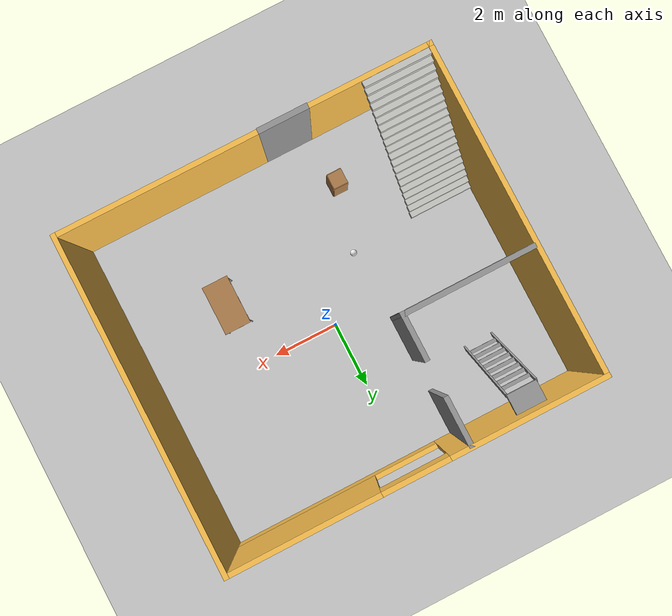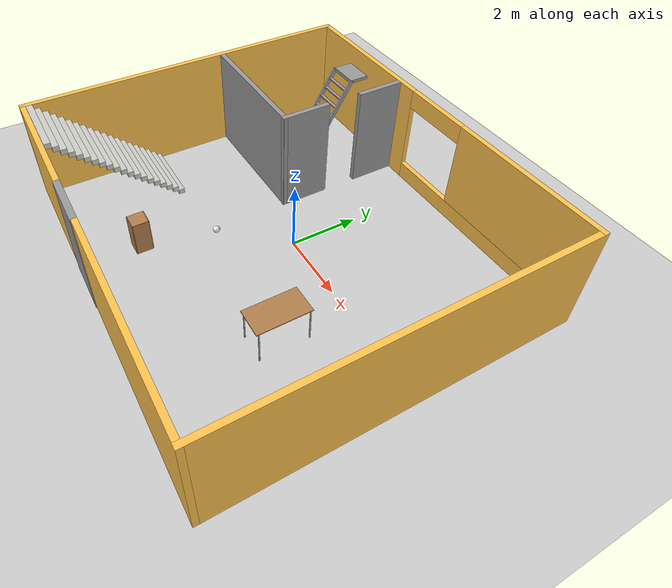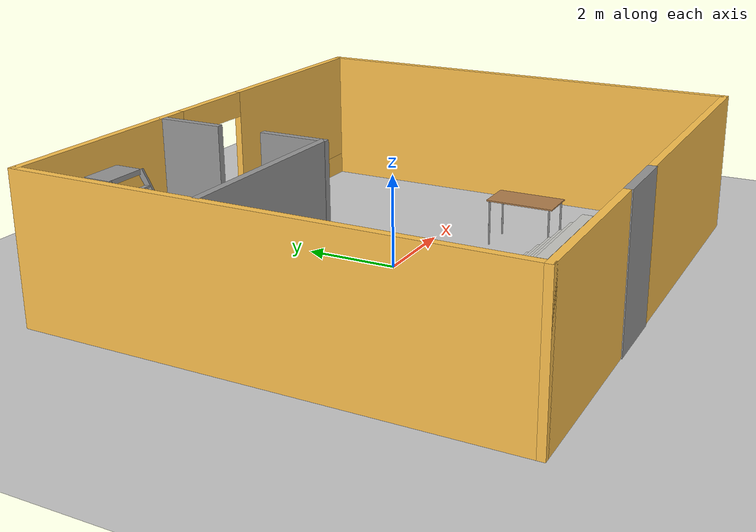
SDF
<sdf version="1.6">
 <world name="default">
  <light name="sun" type="directional">
   <pose>0 0 10 0 -0 0</pose>
   <diffuse>0.8 0.8 0.8 1</diffuse>
   <specular>0.2 0.2 0.2 1</specular>
   <attenuation>
    <range>1000</range>
    <constant>0.9</constant>
    <linear>0.01</linear>
    <quadratic>0.001</quadratic>
   </attenuation>
   <direction>-0.5 0.1 -0.9</direction>
  </light>
  <model name="ground_plane">
   <static>1</static>
   <link name="link">
    <collision name="collision">
     <geometry><plane><normal>0 0 1</normal><size>100 100</size></plane></geometry>
     <surface>
      <contact><collide_bitmask>65535</collide_bitmask></contact>
      <friction><ode><mu>100</mu><mu2>50</mu2></ode></friction>
     </surface>
    </collision>
    <visual name="visual">
     <cast_shadows>0</cast_shadows>
     <geometry><plane><normal>0 0 1</normal><size>100 100</size></plane></geometry>
     <material>
      <script><uri>file://media/materials/scripts/gazebo.material</uri><name>Gazebo/Grey</name></script>
     </material>
    </visual>
   </link>
  </model>
  <gravity>0 0 -9.8</gravity>
  <magnetic_field>6e-06 2.3e-05 -4.2e-05</magnetic_field>
  <atmosphere type="adiabatic"/>
  <physics name="default_physics" default="0" type="ode">
   <max_step_size>0.001</max_step_size>
   <real_time_factor>1</real_time_factor>
   <real_time_update_rate>1000</real_time_update_rate>
  </physics>
  <scene><ambient>0.4 0.4 0.4 1</ambient><background>0.7 0.7 0.7 1</background><shadows>1</shadows></scene>
  <audio><device>default</device></audio>
  <spherical_coordinates>
   <surface_model>EARTH_WGS84</surface_model>
   <latitude_deg>0</latitude_deg>
   <longitude_deg>0</longitude_deg>
   <elevation>0</elevation>
   <heading_deg>0</heading_deg>
  </spherical_coordinates>
  <model name="single_floor">
   <link name="Door_0">
    <pose>-1.18 -4.9275 0 0 -0 0</pose>
    <visual name="Door_0_Visual">
     <pose>0 0 1.525 0 -0 0</pose>
     <geometry><box><size>1.5 0.17 3.05</size></box></geometry>
     <material>
      <script><uri>file://media/materials/scripts/gazebo.material</uri><name>Gazebo/Grey</name></script>
     </material>
    </visual>
    <collision name="Door_0_Collision">
     <pose>0 0 1.525 0 -0 0</pose>
     <geometry><box><size>1.5 0.17 3.05</size></box></geometry>
     <surface>
      <friction>
       <ode><mu>1</mu><mu2>1</mu2><fdir1>0 0 0</fdir1><slip1>0</slip1><slip2>0</slip2></ode>
       <torsional>
        <coefficient>1</coefficient>
        <patch_radius>0</patch_radius>
        <surface_radius>0</surface_radius>
        <use_patch_radius>1</use_patch_radius>
        <ode><slip>0</slip></ode>
       </torsional>
      </friction>
      <bounce><restitution_coefficient>0</restitution_coefficient><threshold>1e+06</threshold></bounce>
      <contact>
       <collide_without_contact>0</collide_without_contact>
       <collide_without_contact_bitmask>1</collide_without_contact_bitmask>
       <collide_bitmask>1</collide_bitmask>
       <ode>
        <soft_cfm>0</soft_cfm>
        <soft_erp>0.2</soft_erp>
        <kp>1e+13</kp>
        <kd>1</kd>
        <max_vel>0.01</max_vel>
        <min_depth>0</min_depth>
       </ode>
       <bullet>
        <split_impulse>1</split_impulse>
        <split_impulse_penetration_threshold>-0.01</split_impulse_penetration_threshold>
        <soft_cfm>0</soft_cfm>
        <soft_erp>0.2</soft_erp>
        <kp>1e+13</kp>
        <kd>1</kd>
       </bullet>
      </contact>
     </surface>
    </collision>
   </link>
   <link name="Stairs_3">
    <visual name="Stairs_3_Visual_0">
     <pose>-4.47 -1.41525 0.07625 0 -0 0</pose>
     <geometry><box><size>2 0.1755 0.1525</size></box></geometry>
     <material>
      <script><uri>file://media/materials/scripts/gazebo.material</uri><name>Gazebo/CeilingTiled</name></script>
      <ambient>0.760784 0.662745 0.627451 1</ambient>
     </material>
     <meta><layer>0</layer></meta>
    </visual>
    <visual name="Stairs_3_Visual_1">
     <pose>-4.47 -1.59075 0.22875 0 -0 0</pose>
     <geometry><box><size>2 0.1755 0.1525</size></box></geometry>
     <material>
      <script><uri>file://media/materials/scripts/gazebo.material</uri><name>Gazebo/CeilingTiled</name></script>
      <ambient>0.760784 0.662745 0.627451 1</ambient>
     </material>
     <meta><layer>0</layer></meta>
    </visual>
    <visual name="Stairs_3_Visual_2">
     <pose>-4.47 -1.76625 0.38125 0 -0 0</pose>
     <geometry><box><size>2 0.1755 0.1525</size></box></geometry>
     <material>
      <script><uri>file://media/materials/scripts/gazebo.material</uri><name>Gazebo/CeilingTiled</name></script>
      <ambient>0.760784 0.662745 0.627451 1</ambient>
     </material>
     <meta><layer>0</layer></meta>
    </visual>
    <visual name="Stairs_3_Visual_11">
     <pose>-4.47 -3.34575 1.75375 0 -0 0</pose>
     <geometry><box><size>2 0.1755 0.1525</size></box></geometry>
     <material>
      <script><uri>file://media/materials/scripts/gazebo.material</uri><name>Gazebo/CeilingTiled</name></script>
      <ambient>0.760784 0.662745 0.627451 1</ambient>
     </material>
     <meta><layer>0</layer></meta>
    </visual>
    <visual name="Stairs_3_Visual_3">
     <pose>-4.47 -1.94175 0.53375 0 -0 0</pose>
     <geometry><box><size>2 0.1755 0.1525</size></box></geometry>
     <material>
      <script><uri>file://media/materials/scripts/gazebo.material</uri><name>Gazebo/CeilingTiled</name></script>
      <ambient>0.760784 0.662745 0.627451 1</ambient>
     </material>
     <meta><layer>0</layer></meta>
    </visual>
    <visual name="Stairs_3_Visual_4">
     <pose>-4.47 -2.11725 0.68625 0 -0 0</pose>
     <geometry><box><size>2 0.1755 0.1525</size></box></geometry>
     <material>
      <script><uri>file://media/materials/scripts/gazebo.material</uri><name>Gazebo/CeilingTiled</name></script>
      <ambient>0.760784 0.662745 0.627451 1</ambient>
     </material>
     <meta><layer>0</layer></meta>
    </visual>
    <visual name="Stairs_3_Visual_5">
     <pose>-4.47 -2.29275 0.83875 0 -0 0</pose>
     <geometry><box><size>2 0.1755 0.1525</size></box></geometry>
     <material>
      <script><uri>file://media/materials/scripts/gazebo.material</uri><name>Gazebo/CeilingTiled</name></script>
      <ambient>0.760784 0.662745 0.627451 1</ambient>
     </material>
     <meta><layer>0</layer></meta>
    </visual>
    <visual name="Stairs_3_Visual_6">
     <pose>-4.47 -2.46825 0.99125 0 -0 0</pose>
     <geometry><box><size>2 0.1755 0.1525</size></box></geometry>
     <material>
      <script><uri>file://media/materials/scripts/gazebo.material</uri><name>Gazebo/CeilingTiled</name></script>
      <ambient>0.760784 0.662745 0.627451 1</ambient>
     </material>
     <meta><layer>0</layer></meta>
    </visual>
    <visual name="Stairs_3_Visual_7">
     <pose>-4.47 -2.64375 1.14375 0 -0 0</pose>
     <geometry><box><size>2 0.1755 0.1525</size></box></geometry>
     <material>
      <script><uri>file://media/materials/scripts/gazebo.material</uri><name>Gazebo/CeilingTiled</name></script>
      <ambient>0.760784 0.662745 0.627451 1</ambient>
     </material>
     <meta><layer>0</layer></meta>
    </visual>
    <visual name="Stairs_3_Visual_8">
     <pose>-4.47 -2.81925 1.29625 0 -0 0</pose>
     <geometry><box><size>2 0.1755 0.1525</size></box></geometry>
     <material>
      <script><uri>file://media/materials/scripts/gazebo.material</uri><name>Gazebo/CeilingTiled</name></script>
      <ambient>0.760784 0.662745 0.627451 1</ambient>
     </material>
     <meta><layer>0</layer></meta>
    </visual>
    <visual name="Stairs_3_Visual_9">
     <pose>-4.47 -2.99475 1.44875 0 -0 0</pose>
     <geometry><box><size>2 0.1755 0.1525</size></box></geometry>
     <material>
      <script><uri>file://media/materials/scripts/gazebo.material</uri><name>Gazebo/CeilingTiled</name></script>
      <ambient>0.760784 0.662745 0.627451 1</ambient>
     </material>
     <meta><layer>0</layer></meta>
    </visual>
    <visual name="Stairs_3_Visual_10">
     <pose>-4.47 -3.17025 1.60125 0 -0 0</pose>
     <geometry><box><size>2 0.1755 0.1525</size></box></geometry>
     <material>
      <script><uri>file://media/materials/scripts/gazebo.material</uri><name>Gazebo/CeilingTiled</name></script>
      <ambient>0.760784 0.662745 0.627451 1</ambient>
     </material>
     <meta><layer>0</layer></meta>
    </visual>
    <visual name="Stairs_3_Visual_12">
     <pose>-4.47 -3.52125 1.90625 0 -0 0</pose>
     <geometry><box><size>2 0.1755 0.1525</size></box></geometry>
     <material>
      <script><uri>file://media/materials/scripts/gazebo.material</uri><name>Gazebo/CeilingTiled</name></script>
      <ambient>0.760784 0.662745 0.627451 1</ambient>
     </material>
     <meta><layer>0</layer></meta>
    </visual>
    <visual name="Stairs_3_Visual_13">
     <pose>-4.47 -3.69675 2.05875 0 -0 0</pose>
     <geometry><box><size>2 0.1755 0.1525</size></box></geometry>
     <material>
      <script><uri>file://media/materials/scripts/gazebo.material</uri><name>Gazebo/CeilingTiled</name></script>
      <ambient>0.760784 0.662745 0.627451 1</ambient>
     </material>
     <meta><layer>0</layer></meta>
    </visual>
    <visual name="Stairs_3_Visual_14">
     <pose>-4.47 -3.87225 2.21125 0 -0 0</pose>
     <geometry><box><size>2 0.1755 0.1525</size></box></geometry>
     <material>
      <script><uri>file://media/materials/scripts/gazebo.material</uri><name>Gazebo/CeilingTiled</name></script>
      <ambient>0.760784 0.662745 0.627451 1</ambient>
     </material>
     <meta><layer>0</layer></meta>
    </visual>
    <visual name="Stairs_3_Visual_15">
     <pose>-4.47 -4.04775 2.36375 0 -0 0</pose>
     <geometry><box><size>2 0.1755 0.1525</size></box></geometry>
     <material>
      <script><uri>file://media/materials/scripts/gazebo.material</uri><name>Gazebo/CeilingTiled</name></script>
      <ambient>0.760784 0.662745 0.627451 1</ambient>
     </material>
     <meta><layer>0</layer></meta>
    </visual>
    <visual name="Stairs_3_Visual_16">
     <pose>-4.47 -4.22325 2.51625 0 -0 0</pose>
     <geometry><box><size>2 0.1755 0.1525</size></box></geometry>
     <material>
      <script><uri>file://media/materials/scripts/gazebo.material</uri><name>Gazebo/CeilingTiled</name></script>
      <ambient>0.760784 0.662745 0.627451 1</ambient>
     </material>
     <meta><layer>0</layer></meta>
    </visual>
    <visual name="Stairs_3_Visual_17">
     <pose>-4.47 -4.39875 2.66875 0 -0 0</pose>
     <geometry><box><size>2 0.1755 0.1525</size></box></geometry>
     <material>
      <script><uri>file://media/materials/scripts/gazebo.material</uri><name>Gazebo/CeilingTiled</name></script>
      <ambient>0.760784 0.662745 0.627451 1</ambient>
     </material>
     <meta><layer>0</layer></meta>
    </visual>
    <visual name="Stairs_3_Visual_18">
     <pose>-4.47 -4.57425 2.82125 0 -0 0</pose>
     <geometry><box><size>2 0.1755 0.1525</size></box></geometry>
     <material>
      <script><uri>file://media/materials/scripts/gazebo.material</uri><name>Gazebo/CeilingTiled</name></script>
      <ambient>0.760784 0.662745 0.627451 1</ambient>
     </material>
     <meta><layer>0</layer></meta>
    </visual>
    <visual name="Stairs_3_Visual_19">
     <pose>-4.47 -4.74975 2.97375 0 -0 0</pose>
     <geometry><box><size>2 0.1755 0.1525</size></box></geometry>
     <material>
      <script><uri>file://media/materials/scripts/gazebo.material</uri><name>Gazebo/CeilingTiled</name></script>
      <ambient>0.760784 0.662745 0.627451 1</ambient>
     </material>
     <meta><layer>0</layer></meta>
    </visual>
    <collision name="Stairs_3_Collision_0">
     <pose>-4.47 -1.41525 0.07625 0 -0 0</pose>
     <geometry><box><size>2 0.1755 0.1525</size></box></geometry>
     <surface>
      <friction>
       <ode><mu>1</mu><mu2>1</mu2><fdir1>0 0 0</fdir1><slip1>0</slip1><slip2>0</slip2></ode>
       <torsional>
        <coefficient>1</coefficient>
        <patch_radius>0</patch_radius>
        <surface_radius>0</surface_radius>
        <use_patch_radius>1</use_patch_radius>
        <ode><slip>0</slip></ode>
       </torsional>
      </friction>
      <bounce><restitution_coefficient>0</restitution_coefficient><threshold>1e+06</threshold></bounce>
      <contact>
       <collide_without_contact>0</collide_without_contact>
       <collide_without_contact_bitmask>1</collide_without_contact_bitmask>
       <collide_bitmask>1</collide_bitmask>
       <ode>
        <soft_cfm>0</soft_cfm>
        <soft_erp>0.2</soft_erp>
        <kp>1e+13</kp>
        <kd>1</kd>
        <max_vel>0.01</max_vel>
        <min_depth>0</min_depth>
       </ode>
       <bullet>
        <split_impulse>1</split_impulse>
        <split_impulse_penetration_threshold>-0.01</split_impulse_penetration_threshold>
        <soft_cfm>0</soft_cfm>
        <soft_erp>0.2</soft_erp>
        <kp>1e+13</kp>
        <kd>1</kd>
       </bullet>
      </contact>
     </surface>
    </collision>
    <collision name="Stairs_3_Collision_1">
     <pose>-4.47 -1.59075 0.22875 0 -0 0</pose>
     <geometry><box><size>2 0.1755 0.1525</size></box></geometry>
     <surface>
      <friction>
       <ode><mu>1</mu><mu2>1</mu2><fdir1>0 0 0</fdir1><slip1>0</slip1><slip2>0</slip2></ode>
       <torsional>
        <coefficient>1</coefficient>
        <patch_radius>0</patch_radius>
        <surface_radius>0</surface_radius>
        <use_patch_radius>1</use_patch_radius>
        <ode><slip>0</slip></ode>
       </torsional>
      </friction>
      <bounce><restitution_coefficient>0</restitution_coefficient><threshold>1e+06</threshold></bounce>
      <contact>
       <collide_without_contact>0</collide_without_contact>
       <collide_without_contact_bitmask>1</collide_without_contact_bitmask>
       <collide_bitmask>1</collide_bitmask>
       <ode>
        <soft_cfm>0</soft_cfm>
        <soft_erp>0.2</soft_erp>
        <kp>1e+13</kp>
        <kd>1</kd>
        <max_vel>0.01</max_vel>
        <min_depth>0</min_depth>
       </ode>
       <bullet>
        <split_impulse>1</split_impulse>
        <split_impulse_penetration_threshold>-0.01</split_impulse_penetration_threshold>
        <soft_cfm>0</soft_cfm>
        <soft_erp>0.2</soft_erp>
        <kp>1e+13</kp>
        <kd>1</kd>
       </bullet>
      </contact>
     </surface>
    </collision>
    <collision name="Stairs_3_Collision_2">
     <pose>-4.47 -1.76625 0.38125 0 -0 0</pose>
     <geometry><box><size>2 0.1755 0.1525</size></box></geometry>
     <surface>
      <friction>
       <ode><mu>1</mu><mu2>1</mu2><fdir1>0 0 0</fdir1><slip1>0</slip1><slip2>0</slip2></ode>
       <torsional>
        <coefficient>1</coefficient>
        <patch_radius>0</patch_radius>
        <surface_radius>0</surface_radius>
        <use_patch_radius>1</use_patch_radius>
        <ode><slip>0</slip></ode>
       </torsional>
      </friction>
      <bounce><restitution_coefficient>0</restitution_coefficient><threshold>1e+06</threshold></bounce>
      <contact>
       <collide_without_contact>0</collide_without_contact>
       <collide_without_contact_bitmask>1</collide_without_contact_bitmask>
       <collide_bitmask>1</collide_bitmask>
       <ode>
        <soft_cfm>0</soft_cfm>
        <soft_erp>0.2</soft_erp>
        <kp>1e+13</kp>
        <kd>1</kd>
        <max_vel>0.01</max_vel>
        <min_depth>0</min_depth>
       </ode>
       <bullet>
        <split_impulse>1</split_impulse>
        <split_impulse_penetration_threshold>-0.01</split_impulse_penetration_threshold>
        <soft_cfm>0</soft_cfm>
        <soft_erp>0.2</soft_erp>
        <kp>1e+13</kp>
        <kd>1</kd>
       </bullet>
      </contact>
     </surface>
    </collision>
    <collision name="Stairs_3_Collision_3">
     <pose>-4.47 -1.94175 0.53375 0 -0 0</pose>
     <geometry><box><size>2 0.1755 0.1525</size></box></geometry>
     <surface>
      <friction>
       <ode><mu>1</mu><mu2>1</mu2><fdir1>0 0 0</fdir1><slip1>0</slip1><slip2>0</slip2></ode>
       <torsional>
        <coefficient>1</coefficient>
        <patch_radius>0</patch_radius>
        <surface_radius>0</surface_radius>
        <use_patch_radius>1</use_patch_radius>
        <ode><slip>0</slip></ode>
       </torsional>
      </friction>
      <bounce><restitution_coefficient>0</restitution_coefficient><threshold>1e+06</threshold></bounce>
      <contact>
       <collide_without_contact>0</collide_without_contact>
       <collide_without_contact_bitmask>1</collide_without_contact_bitmask>
       <collide_bitmask>1</collide_bitmask>
       <ode>
        <soft_cfm>0</soft_cfm>
        <soft_erp>0.2</soft_erp>
        <kp>1e+13</kp>
        <kd>1</kd>
        <max_vel>0.01</max_vel>
        <min_depth>0</min_depth>
       </ode>
       <bullet>
        <split_impulse>1</split_impulse>
        <split_impulse_penetration_threshold>-0.01</split_impulse_penetration_threshold>
        <soft_cfm>0</soft_cfm>
        <soft_erp>0.2</soft_erp>
        <kp>1e+13</kp>
        <kd>1</kd>
       </bullet>
      </contact>
     </surface>
    </collision>
    <collision name="Stairs_3_Collision_4">
     <pose>-4.47 -2.11725 0.68625 0 -0 0</pose>
     <geometry><box><size>2 0.1755 0.1525</size></box></geometry>
     <surface>
      <friction>
       <ode><mu>1</mu><mu2>1</mu2><fdir1>0 0 0</fdir1><slip1>0</slip1><slip2>0</slip2></ode>
       <torsional>
        <coefficient>1</coefficient>
        <patch_radius>0</patch_radius>
        <surface_radius>0</surface_radius>
        <use_patch_radius>1</use_patch_radius>
        <ode><slip>0</slip></ode>
       </torsional>
      </friction>
      <bounce><restitution_coefficient>0</restitution_coefficient><threshold>1e+06</threshold></bounce>
      <contact>
       <collide_without_contact>0</collide_without_contact>
       <collide_without_contact_bitmask>1</collide_without_contact_bitmask>
       <collide_bitmask>1</collide_bitmask>
       <ode>
        <soft_cfm>0</soft_cfm>
        <soft_erp>0.2</soft_erp>
        <kp>1e+13</kp>
        <kd>1</kd>
        <max_vel>0.01</max_vel>
        <min_depth>0</min_depth>
       </ode>
       <bullet>
        <split_impulse>1</split_impulse>
        <split_impulse_penetration_threshold>-0.01</split_impulse_penetration_threshold>
        <soft_cfm>0</soft_cfm>
        <soft_erp>0.2</soft_erp>
        <kp>1e+13</kp>
        <kd>1</kd>
       </bullet>
      </contact>
     </surface>
    </collision>
    <collision name="Stairs_3_Collision_5">
     <pose>-4.47 -2.29275 0.83875 0 -0 0</pose>
     <geometry><box><size>2 0.1755 0.1525</size></box></geometry>
     <surface>
      <friction>
       <ode><mu>1</mu><mu2>1</mu2><fdir1>0 0 0</fdir1><slip1>0</slip1><slip2>0</slip2></ode>
       <torsional>
        <coefficient>1</coefficient>
        <patch_radius>0</patch_radius>
        <surface_radius>0</surface_radius>
        <use_patch_radius>1</use_patch_radius>
        <ode><slip>0</slip></ode>
       </torsional>
      </friction>
      <bounce><restitution_coefficient>0</restitution_coefficient><threshold>1e+06</threshold></bounce>
      <contact>
       <collide_without_contact>0</collide_without_contact>
       <collide_without_contact_bitmask>1</collide_without_contact_bitmask>
       <collide_bitmask>1</collide_bitmask>
       <ode>
        <soft_cfm>0</soft_cfm>
        <soft_erp>0.2</soft_erp>
        <kp>1e+13</kp>
        <kd>1</kd>
        <max_vel>0.01</max_vel>
        <min_depth>0</min_depth>
       </ode>
       <bullet>
        <split_impulse>1</split_impulse>
        <split_impulse_penetration_threshold>-0.01</split_impulse_penetration_threshold>
        <soft_cfm>0</soft_cfm>
        <soft_erp>0.2</soft_erp>
        <kp>1e+13</kp>
        <kd>1</kd>
       </bullet>
      </contact>
     </surface>
    </collision>
    <collision name="Stairs_3_Collision_6">
     <pose>-4.47 -2.46825 0.99125 0 -0 0</pose>
     <geometry><box><size>2 0.1755 0.1525</size></box></geometry>
     <surface>
      <friction>
       <ode><mu>1</mu><mu2>1</mu2><fdir1>0 0 0</fdir1><slip1>0</slip1><slip2>0</slip2></ode>
       <torsional>
        <coefficient>1</coefficient>
        <patch_radius>0</patch_radius>
        <surface_radius>0</surface_radius>
        <use_patch_radius>1</use_patch_radius>
        <ode><slip>0</slip></ode>
       </torsional>
      </friction>
      <bounce><restitution_coefficient>0</restitution_coefficient><threshold>1e+06</threshold></bounce>
      <contact>
       <collide_without_contact>0</collide_without_contact>
       <collide_without_contact_bitmask>1</collide_without_contact_bitmask>
       <collide_bitmask>1</collide_bitmask>
       <ode>
        <soft_cfm>0</soft_cfm>
        <soft_erp>0.2</soft_erp>
        <kp>1e+13</kp>
        <kd>1</kd>
        <max_vel>0.01</max_vel>
        <min_depth>0</min_depth>
       </ode>
       <bullet>
        <split_impulse>1</split_impulse>
        <split_impulse_penetration_threshold>-0.01</split_impulse_penetration_threshold>
        <soft_cfm>0</soft_cfm>
        <soft_erp>0.2</soft_erp>
        <kp>1e+13</kp>
        <kd>1</kd>
       </bullet>
      </contact>
     </surface>
    </collision>
    <collision name="Stairs_3_Collision_7">
     <pose>-4.47 -2.64375 1.14375 0 -0 0</pose>
     <geometry><box><size>2 0.1755 0.1525</size></box></geometry>
     <surface>
      <friction>
       <ode><mu>1</mu><mu2>1</mu2><fdir1>0 0 0</fdir1><slip1>0</slip1><slip2>0</slip2></ode>
       <torsional>
        <coefficient>1</coefficient>
        <patch_radius>0</patch_radius>
        <surface_radius>0</surface_radius>
        <use_patch_radius>1</use_patch_radius>
        <ode><slip>0</slip></ode>
       </torsional>
      </friction>
      <bounce><restitution_coefficient>0</restitution_coefficient><threshold>1e+06</threshold></bounce>
      <contact>
       <collide_without_contact>0</collide_without_contact>
       <collide_without_contact_bitmask>1</collide_without_contact_bitmask>
       <collide_bitmask>1</collide_bitmask>
       <ode>
        <soft_cfm>0</soft_cfm>
        <soft_erp>0.2</soft_erp>
        <kp>1e+13</kp>
        <kd>1</kd>
        <max_vel>0.01</max_vel>
        <min_depth>0</min_depth>
       </ode>
       <bullet>
        <split_impulse>1</split_impulse>
        <split_impulse_penetration_threshold>-0.01</split_impulse_penetration_threshold>
        <soft_cfm>0</soft_cfm>
        <soft_erp>0.2</soft_erp>
        <kp>1e+13</kp>
        <kd>1</kd>
       </bullet>
      </contact>
     </surface>
    </collision>
    <collision name="Stairs_3_Collision_8">
     <pose>-4.47 -2.81925 1.29625 0 -0 0</pose>
     <geometry><box><size>2 0.1755 0.1525</size></box></geometry>
     <surface>
      <friction>
       <ode><mu>1</mu><mu2>1</mu2><fdir1>0 0 0</fdir1><slip1>0</slip1><slip2>0</slip2></ode>
       <torsional>
        <coefficient>1</coefficient>
        <patch_radius>0</patch_radius>
        <surface_radius>0</surface_radius>
        <use_patch_radius>1</use_patch_radius>
        <ode><slip>0</slip></ode>
       </torsional>
      </friction>
      <bounce><restitution_coefficient>0</restitution_coefficient><threshold>1e+06</threshold></bounce>
      <contact>
       <collide_without_contact>0</collide_without_contact>
       <collide_without_contact_bitmask>1</collide_without_contact_bitmask>
       <collide_bitmask>1</collide_bitmask>
       <ode>
        <soft_cfm>0</soft_cfm>
        <soft_erp>0.2</soft_erp>
        <kp>1e+13</kp>
        <kd>1</kd>
        <max_vel>0.01</max_vel>
        <min_depth>0</min_depth>
       </ode>
       <bullet>
        <split_impulse>1</split_impulse>
        <split_impulse_penetration_threshold>-0.01</split_impulse_penetration_threshold>
        <soft_cfm>0</soft_cfm>
        <soft_erp>0.2</soft_erp>
        <kp>1e+13</kp>
        <kd>1</kd>
       </bullet>
      </contact>
     </surface>
    </collision>
    <collision name="Stairs_3_Collision_9">
     <pose>-4.47 -2.99475 1.44875 0 -0 0</pose>
     <geometry><box><size>2 0.1755 0.1525</size></box></geometry>
     <surface>
      <friction>
       <ode><mu>1</mu><mu2>1</mu2><fdir1>0 0 0</fdir1><slip1>0</slip1><slip2>0</slip2></ode>
       <torsional>
        <coefficient>1</coefficient>
        <patch_radius>0</patch_radius>
        <surface_radius>0</surface_radius>
        <use_patch_radius>1</use_patch_radius>
        <ode><slip>0</slip></ode>
       </torsional>
      </friction>
      <bounce><restitution_coefficient>0</restitution_coefficient><threshold>1e+06</threshold></bounce>
      <contact>
       <collide_without_contact>0</collide_without_contact>
       <collide_without_contact_bitmask>1</collide_without_contact_bitmask>
       <collide_bitmask>1</collide_bitmask>
       <ode>
        <soft_cfm>0</soft_cfm>
        <soft_erp>0.2</soft_erp>
        <kp>1e+13</kp>
        <kd>1</kd>
        <max_vel>0.01</max_vel>
        <min_depth>0</min_depth>
       </ode>
       <bullet>
        <split_impulse>1</split_impulse>
        <split_impulse_penetration_threshold>-0.01</split_impulse_penetration_threshold>
        <soft_cfm>0</soft_cfm>
        <soft_erp>0.2</soft_erp>
        <kp>1e+13</kp>
        <kd>1</kd>
       </bullet>
      </contact>
     </surface>
    </collision>
    <collision name="Stairs_3_Collision_10">
     <pose>-4.47 -3.17025 1.60125 0 -0 0</pose>
     <geometry><box><size>2 0.1755 0.1525</size></box></geometry>
     <surface>
      <friction>
       <ode><mu>1</mu><mu2>1</mu2><fdir1>0 0 0</fdir1><slip1>0</slip1><slip2>0</slip2></ode>
       <torsional>
        <coefficient>1</coefficient>
        <patch_radius>0</patch_radius>
        <surface_radius>0</surface_radius>
        <use_patch_radius>1</use_patch_radius>
        <ode><slip>0</slip></ode>
       </torsional>
      </friction>
      <bounce><restitution_coefficient>0</restitution_coefficient><threshold>1e+06</threshold></bounce>
      <contact>
       <collide_without_contact>0</collide_without_contact>
       <collide_without_contact_bitmask>1</collide_without_contact_bitmask>
       <collide_bitmask>1</collide_bitmask>
       <ode>
        <soft_cfm>0</soft_cfm>
        <soft_erp>0.2</soft_erp>
        <kp>1e+13</kp>
        <kd>1</kd>
        <max_vel>0.01</max_vel>
        <min_depth>0</min_depth>
       </ode>
       <bullet>
        <split_impulse>1</split_impulse>
        <split_impulse_penetration_threshold>-0.01</split_impulse_penetration_threshold>
        <soft_cfm>0</soft_cfm>
        <soft_erp>0.2</soft_erp>
        <kp>1e+13</kp>
        <kd>1</kd>
       </bullet>
      </contact>
     </surface>
    </collision>
    <collision name="Stairs_3_Collision_11">
     <pose>-4.47 -3.34575 1.75375 0 -0 0</pose>
     <geometry><box><size>2 0.1755 0.1525</size></box></geometry>
     <surface>
      <friction>
       <ode><mu>1</mu><mu2>1</mu2><fdir1>0 0 0</fdir1><slip1>0</slip1><slip2>0</slip2></ode>
       <torsional>
        <coefficient>1</coefficient>
        <patch_radius>0</patch_radius>
        <surface_radius>0</surface_radius>
        <use_patch_radius>1</use_patch_radius>
        <ode><slip>0</slip></ode>
       </torsional>
      </friction>
      <bounce><restitution_coefficient>0</restitution_coefficient><threshold>1e+06</threshold></bounce>
      <contact>
       <collide_without_contact>0</collide_without_contact>
       <collide_without_contact_bitmask>1</collide_without_contact_bitmask>
       <collide_bitmask>1</collide_bitmask>
       <ode>
        <soft_cfm>0</soft_cfm>
        <soft_erp>0.2</soft_erp>
        <kp>1e+13</kp>
        <kd>1</kd>
        <max_vel>0.01</max_vel>
        <min_depth>0</min_depth>
       </ode>
       <bullet>
        <split_impulse>1</split_impulse>
        <split_impulse_penetration_threshold>-0.01</split_impulse_penetration_threshold>
        <soft_cfm>0</soft_cfm>
        <soft_erp>0.2</soft_erp>
        <kp>1e+13</kp>
        <kd>1</kd>
       </bullet>
      </contact>
     </surface>
    </collision>
    <collision name="Stairs_3_Collision_12">
     <pose>-4.47 -3.52125 1.90625 0 -0 0</pose>
     <geometry><box><size>2 0.1755 0.1525</size></box></geometry>
     <surface>
      <friction>
       <ode><mu>1</mu><mu2>1</mu2><fdir1>0 0 0</fdir1><slip1>0</slip1><slip2>0</slip2></ode>
       <torsional>
        <coefficient>1</coefficient>
        <patch_radius>0</patch_radius>
        <surface_radius>0</surface_radius>
        <use_patch_radius>1</use_patch_radius>
        <ode><slip>0</slip></ode>
       </torsional>
      </friction>
      <bounce><restitution_coefficient>0</restitution_coefficient><threshold>1e+06</threshold></bounce>
      <contact>
       <collide_without_contact>0</collide_without_contact>
       <collide_without_contact_bitmask>1</collide_without_contact_bitmask>
       <collide_bitmask>1</collide_bitmask>
       <ode>
        <soft_cfm>0</soft_cfm>
        <soft_erp>0.2</soft_erp>
        <kp>1e+13</kp>
        <kd>1</kd>
        <max_vel>0.01</max_vel>
        <min_depth>0</min_depth>
       </ode>
       <bullet>
        <split_impulse>1</split_impulse>
        <split_impulse_penetration_threshold>-0.01</split_impulse_penetration_threshold>
        <soft_cfm>0</soft_cfm>
        <soft_erp>0.2</soft_erp>
        <kp>1e+13</kp>
        <kd>1</kd>
       </bullet>
      </contact>
     </surface>
    </collision>
    <collision name="Stairs_3_Collision_13">
     <pose>-4.47 -3.69675 2.05875 0 -0 0</pose>
     <geometry><box><size>2 0.1755 0.1525</size></box></geometry>
     <surface>
      <friction>
       <ode><mu>1</mu><mu2>1</mu2><fdir1>0 0 0</fdir1><slip1>0</slip1><slip2>0</slip2></ode>
       <torsional>
        <coefficient>1</coefficient>
        <patch_radius>0</patch_radius>
        <surface_radius>0</surface_radius>
        <use_patch_radius>1</use_patch_radius>
        <ode><slip>0</slip></ode>
       </torsional>
      </friction>
      <bounce><restitution_coefficient>0</restitution_coefficient><threshold>1e+06</threshold></bounce>
      <contact>
       <collide_without_contact>0</collide_without_contact>
       <collide_without_contact_bitmask>1</collide_without_contact_bitmask>
       <collide_bitmask>1</collide_bitmask>
       <ode>
        <soft_cfm>0</soft_cfm>
        <soft_erp>0.2</soft_erp>
        <kp>1e+13</kp>
        <kd>1</kd>
        <max_vel>0.01</max_vel>
        <min_depth>0</min_depth>
       </ode>
       <bullet>
        <split_impulse>1</split_impulse>
        <split_impulse_penetration_threshold>-0.01</split_impulse_penetration_threshold>
        <soft_cfm>0</soft_cfm>
        <soft_erp>0.2</soft_erp>
        <kp>1e+13</kp>
        <kd>1</kd>
       </bullet>
      </contact>
     </surface>
    </collision>
    <collision name="Stairs_3_Collision_14">
     <pose>-4.47 -3.87225 2.21125 0 -0 0</pose>
     <geometry><box><size>2 0.1755 0.1525</size></box></geometry>
     <surface>
      <friction>
       <ode><mu>1</mu><mu2>1</mu2><fdir1>0 0 0</fdir1><slip1>0</slip1><slip2>0</slip2></ode>
       <torsional>
        <coefficient>1</coefficient>
        <patch_radius>0</patch_radius>
        <surface_radius>0</surface_radius>
        <use_patch_radius>1</use_patch_radius>
        <ode><slip>0</slip></ode>
       </torsional>
      </friction>
      <bounce><restitution_coefficient>0</restitution_coefficient><threshold>1e+06</threshold></bounce>
      <contact>
       <collide_without_contact>0</collide_without_contact>
       <collide_without_contact_bitmask>1</collide_without_contact_bitmask>
       <collide_bitmask>1</collide_bitmask>
       <ode>
        <soft_cfm>0</soft_cfm>
        <soft_erp>0.2</soft_erp>
        <kp>1e+13</kp>
        <kd>1</kd>
        <max_vel>0.01</max_vel>
        <min_depth>0</min_depth>
       </ode>
       <bullet>
        <split_impulse>1</split_impulse>
        <split_impulse_penetration_threshold>-0.01</split_impulse_penetration_threshold>
        <soft_cfm>0</soft_cfm>
        <soft_erp>0.2</soft_erp>
        <kp>1e+13</kp>
        <kd>1</kd>
       </bullet>
      </contact>
     </surface>
    </collision>
    <collision name="Stairs_3_Collision_15">
     <pose>-4.47 -4.04775 2.36375 0 -0 0</pose>
     <geometry><box><size>2 0.1755 0.1525</size></box></geometry>
     <surface>
      <friction>
       <ode><mu>1</mu><mu2>1</mu2><fdir1>0 0 0</fdir1><slip1>0</slip1><slip2>0</slip2></ode>
       <torsional>
        <coefficient>1</coefficient>
        <patch_radius>0</patch_radius>
        <surface_radius>0</surface_radius>
        <use_patch_radius>1</use_patch_radius>
        <ode><slip>0</slip></ode>
       </torsional>
      </friction>
      <bounce><restitution_coefficient>0</restitution_coefficient><threshold>1e+06</threshold></bounce>
      <contact>
       <collide_without_contact>0</collide_without_contact>
       <collide_without_contact_bitmask>1</collide_without_contact_bitmask>
       <collide_bitmask>1</collide_bitmask>
       <ode>
        <soft_cfm>0</soft_cfm>
        <soft_erp>0.2</soft_erp>
        <kp>1e+13</kp>
        <kd>1</kd>
        <max_vel>0.01</max_vel>
        <min_depth>0</min_depth>
       </ode>
       <bullet>
        <split_impulse>1</split_impulse>
        <split_impulse_penetration_threshold>-0.01</split_impulse_penetration_threshold>
        <soft_cfm>0</soft_cfm>
        <soft_erp>0.2</soft_erp>
        <kp>1e+13</kp>
        <kd>1</kd>
       </bullet>
      </contact>
     </surface>
    </collision>
    <collision name="Stairs_3_Collision_16">
     <pose>-4.47 -4.22325 2.51625 0 -0 0</pose>
     <geometry><box><size>2 0.1755 0.1525</size></box></geometry>
     <surface>
      <friction>
       <ode><mu>1</mu><mu2>1</mu2><fdir1>0 0 0</fdir1><slip1>0</slip1><slip2>0</slip2></ode>
       <torsional>
        <coefficient>1</coefficient>
        <patch_radius>0</patch_radius>
        <surface_radius>0</surface_radius>
        <use_patch_radius>1</use_patch_radius>
        <ode><slip>0</slip></ode>
       </torsional>
      </friction>
      <bounce><restitution_coefficient>0</restitution_coefficient><threshold>1e+06</threshold></bounce>
      <contact>
       <collide_without_contact>0</collide_without_contact>
       <collide_without_contact_bitmask>1</collide_without_contact_bitmask>
       <collide_bitmask>1</collide_bitmask>
       <ode>
        <soft_cfm>0</soft_cfm>
        <soft_erp>0.2</soft_erp>
        <kp>1e+13</kp>
        <kd>1</kd>
        <max_vel>0.01</max_vel>
        <min_depth>0</min_depth>
       </ode>
       <bullet>
        <split_impulse>1</split_impulse>
        <split_impulse_penetration_threshold>-0.01</split_impulse_penetration_threshold>
        <soft_cfm>0</soft_cfm>
        <soft_erp>0.2</soft_erp>
        <kp>1e+13</kp>
        <kd>1</kd>
       </bullet>
      </contact>
     </surface>
    </collision>
    <collision name="Stairs_3_Collision_17">
     <pose>-4.47 -4.39875 2.66875 0 -0 0</pose>
     <geometry><box><size>2 0.1755 0.1525</size></box></geometry>
     <surface>
      <friction>
       <ode><mu>1</mu><mu2>1</mu2><fdir1>0 0 0</fdir1><slip1>0</slip1><slip2>0</slip2></ode>
       <torsional>
        <coefficient>1</coefficient>
        <patch_radius>0</patch_radius>
        <surface_radius>0</surface_radius>
        <use_patch_radius>1</use_patch_radius>
        <ode><slip>0</slip></ode>
       </torsional>
      </friction>
      <bounce><restitution_coefficient>0</restitution_coefficient><threshold>1e+06</threshold></bounce>
      <contact>
       <collide_without_contact>0</collide_without_contact>
       <collide_without_contact_bitmask>1</collide_without_contact_bitmask>
       <collide_bitmask>1</collide_bitmask>
       <ode>
        <soft_cfm>0</soft_cfm>
        <soft_erp>0.2</soft_erp>
        <kp>1e+13</kp>
        <kd>1</kd>
        <max_vel>0.01</max_vel>
        <min_depth>0</min_depth>
       </ode>
       <bullet>
        <split_impulse>1</split_impulse>
        <split_impulse_penetration_threshold>-0.01</split_impulse_penetration_threshold>
        <soft_cfm>0</soft_cfm>
        <soft_erp>0.2</soft_erp>
        <kp>1e+13</kp>
        <kd>1</kd>
       </bullet>
      </contact>
     </surface>
    </collision>
    <collision name="Stairs_3_Collision_18">
     <pose>-4.47 -4.57425 2.82125 0 -0 0</pose>
     <geometry><box><size>2 0.1755 0.1525</size></box></geometry>
     <surface>
      <friction>
       <ode><mu>1</mu><mu2>1</mu2><fdir1>0 0 0</fdir1><slip1>0</slip1><slip2>0</slip2></ode>
       <torsional>
        <coefficient>1</coefficient>
        <patch_radius>0</patch_radius>
        <surface_radius>0</surface_radius>
        <use_patch_radius>1</use_patch_radius>
        <ode><slip>0</slip></ode>
       </torsional>
      </friction>
      <bounce><restitution_coefficient>0</restitution_coefficient><threshold>1e+06</threshold></bounce>
      <contact>
       <collide_without_contact>0</collide_without_contact>
       <collide_without_contact_bitmask>1</collide_without_contact_bitmask>
       <collide_bitmask>1</collide_bitmask>
       <ode>
        <soft_cfm>0</soft_cfm>
        <soft_erp>0.2</soft_erp>
        <kp>1e+13</kp>
        <kd>1</kd>
        <max_vel>0.01</max_vel>
        <min_depth>0</min_depth>
       </ode>
       <bullet>
        <split_impulse>1</split_impulse>
        <split_impulse_penetration_threshold>-0.01</split_impulse_penetration_threshold>
        <soft_cfm>0</soft_cfm>
        <soft_erp>0.2</soft_erp>
        <kp>1e+13</kp>
        <kd>1</kd>
       </bullet>
      </contact>
     </surface>
    </collision>
    <collision name="Stairs_3_Collision_19">
     <pose>-4.47 -4.74975 2.97375 0 -0 0</pose>
     <geometry><box><size>2 0.1755 0.1525</size></box></geometry>
     <surface>
      <friction>
       <ode><mu>1</mu><mu2>1</mu2><fdir1>0 0 0</fdir1><slip1>0</slip1><slip2>0</slip2></ode>
       <torsional>
        <coefficient>1</coefficient>
        <patch_radius>0</patch_radius>
        <surface_radius>0</surface_radius>
        <use_patch_radius>1</use_patch_radius>
        <ode><slip>0</slip></ode>
       </torsional>
      </friction>
      <bounce><restitution_coefficient>0</restitution_coefficient><threshold>1e+06</threshold></bounce>
      <contact>
       <collide_without_contact>0</collide_without_contact>
       <collide_without_contact_bitmask>1</collide_without_contact_bitmask>
       <collide_bitmask>1</collide_bitmask>
       <ode>
        <soft_cfm>0</soft_cfm>
        <soft_erp>0.2</soft_erp>
        <kp>1e+13</kp>
        <kd>1</kd>
        <max_vel>0.01</max_vel>
        <min_depth>0</min_depth>
       </ode>
       <bullet>
        <split_impulse>1</split_impulse>
        <split_impulse_penetration_threshold>-0.01</split_impulse_penetration_threshold>
        <soft_cfm>0</soft_cfm>
        <soft_erp>0.2</soft_erp>
        <kp>1e+13</kp>
        <kd>1</kd>
       </bullet>
      </contact>
     </surface>
    </collision>
   </link>
   <link name="Wall_10">
    <pose>5.55 0.0075 0 0 0 -1.5708</pose>
    <visual name="Wall_10_Visual">
     <pose>0 0 1.525 0 -0 0</pose>
     <geometry><box><size>10 0.15 3.05</size></box></geometry>
     <material>
      <script><uri>file://media/materials/scripts/gazebo.material</uri><name>Gazebo/Grey</name></script>
      <ambient>1 0.764706 0.305882 1</ambient>
     </material>
     <meta><layer>0</layer></meta>
    </visual>
    <collision name="Wall_10_Collision">
     <pose>0 0 1.525 0 -0 0</pose>
     <geometry><box><size>10 0.15 3.05</size></box></geometry>
     <surface>
      <friction>
       <ode><mu>1</mu><mu2>1</mu2><fdir1>0 0 0</fdir1><slip1>0</slip1><slip2>0</slip2></ode>
       <torsional>
        <coefficient>1</coefficient>
        <patch_radius>0</patch_radius>
        <surface_radius>0</surface_radius>
        <use_patch_radius>1</use_patch_radius>
        <ode><slip>0</slip></ode>
       </torsional>
      </friction>
      <bounce><restitution_coefficient>0</restitution_coefficient><threshold>1e+06</threshold></bounce>
      <contact>
       <collide_without_contact>0</collide_without_contact>
       <collide_without_contact_bitmask>1</collide_without_contact_bitmask>
       <collide_bitmask>1</collide_bitmask>
       <ode>
        <soft_cfm>0</soft_cfm>
        <soft_erp>0.2</soft_erp>
        <kp>1e+13</kp>
        <kd>1</kd>
        <max_vel>0.01</max_vel>
        <min_depth>0</min_depth>
       </ode>
       <bullet>
        <split_impulse>1</split_impulse>
        <split_impulse_penetration_threshold>-0.01</split_impulse_penetration_threshold>
        <soft_cfm>0</soft_cfm>
        <soft_erp>0.2</soft_erp>
        <kp>1e+13</kp>
        <kd>1</kd>
       </bullet>
      </contact>
     </surface>
    </collision>
   </link>
   <link name="Wall_12">
    <pose>-3.776 -4.9175 0 0 -0 0</pose>
    <visual name="Wall_12_Visual">
     <pose>0 0 1.525 0 -0 0</pose>
     <geometry><box><size>3.698 0.15 3.05</size></box></geometry>
     <material>
      <script><uri>file://media/materials/scripts/gazebo.material</uri><name>Gazebo/Grey</name></script>
      <ambient>1 0.764706 0.305882 1</ambient>
     </material>
     <meta><layer>0</layer></meta>
    </visual>
    <collision name="Wall_12_Collision">
     <pose>0 0 1.525 0 -0 0</pose>
     <geometry><box><size>3.698 0.15 3.05</size></box></geometry>
     <surface>
      <friction>
       <ode><mu>1</mu><mu2>1</mu2><fdir1>0 0 0</fdir1><slip1>0</slip1><slip2>0</slip2></ode>
       <torsional>
        <coefficient>1</coefficient>
        <patch_radius>0</patch_radius>
        <surface_radius>0</surface_radius>
        <use_patch_radius>1</use_patch_radius>
        <ode><slip>0</slip></ode>
       </torsional>
      </friction>
      <bounce><restitution_coefficient>0</restitution_coefficient><threshold>1e+06</threshold></bounce>
      <contact>
       <collide_without_contact>0</collide_without_contact>
       <collide_without_contact_bitmask>1</collide_without_contact_bitmask>
       <collide_bitmask>1</collide_bitmask>
       <ode>
        <soft_cfm>0</soft_cfm>
        <soft_erp>0.2</soft_erp>
        <kp>1e+13</kp>
        <kd>1</kd>
        <max_vel>0.01</max_vel>
        <min_depth>0</min_depth>
       </ode>
       <bullet>
        <split_impulse>1</split_impulse>
        <split_impulse_penetration_threshold>-0.01</split_impulse_penetration_threshold>
        <soft_cfm>0</soft_cfm>
        <soft_erp>0.2</soft_erp>
        <kp>1e+13</kp>
        <kd>1</kd>
       </bullet>
      </contact>
     </surface>
    </collision>
   </link>
   <link name="Wall_15">
    <pose>2.599 -4.9175 0 0 -0 3.14159</pose>
    <visual name="Wall_15_Visual">
     <pose>0 0 1.525 0 -0 0</pose>
     <geometry><box><size>6.052 0.15 3.05</size></box></geometry>
     <material>
      <script><uri>file://media/materials/scripts/gazebo.material</uri><name>Gazebo/Grey</name></script>
      <ambient>1 0.764706 0.305882 1</ambient>
     </material>
     <meta><layer>0</layer></meta>
    </visual>
    <collision name="Wall_15_Collision">
     <pose>0 0 1.525 0 -0 0</pose>
     <geometry><box><size>6.052 0.15 3.05</size></box></geometry>
     <surface>
      <friction>
       <ode><mu>1</mu><mu2>1</mu2><fdir1>0 0 0</fdir1><slip1>0</slip1><slip2>0</slip2></ode>
       <torsional>
        <coefficient>1</coefficient>
        <patch_radius>0</patch_radius>
        <surface_radius>0</surface_radius>
        <use_patch_radius>1</use_patch_radius>
        <ode><slip>0</slip></ode>
       </torsional>
      </friction>
      <bounce><restitution_coefficient>0</restitution_coefficient><threshold>1e+06</threshold></bounce>
      <contact>
       <collide_without_contact>0</collide_without_contact>
       <collide_without_contact_bitmask>1</collide_without_contact_bitmask>
       <collide_bitmask>1</collide_bitmask>
       <ode>
        <soft_cfm>0</soft_cfm>
        <soft_erp>0.2</soft_erp>
        <kp>1e+13</kp>
        <kd>1</kd>
        <max_vel>0.01</max_vel>
        <min_depth>0</min_depth>
       </ode>
       <bullet>
        <split_impulse>1</split_impulse>
        <split_impulse_penetration_threshold>-0.01</split_impulse_penetration_threshold>
        <soft_cfm>0</soft_cfm>
        <soft_erp>0.2</soft_erp>
        <kp>1e+13</kp>
        <kd>1</kd>
       </bullet>
      </contact>
     </surface>
    </collision>
   </link>
   <link name="Wall_17">
    <pose>-1.59 1.7295 0 0 0 -1.5708</pose>
    <visual name="Wall_17_Visual">
     <pose>0 0 1.525 0 -0 0</pose>
     <geometry><box><size>1.456 0.15 3.05</size></box></geometry>
     <material>
      <script><uri>file://media/materials/scripts/gazebo.material</uri><name>Gazebo/Grey</name></script>
      <ambient>1 1 1 1</ambient>
     </material>
     <meta><layer>0</layer></meta>
    </visual>
    <collision name="Wall_17_Collision">
     <pose>0 0 1.525 0 -0 0</pose>
     <geometry><box><size>1.456 0.15 3.05</size></box></geometry>
     <surface>
      <friction>
       <ode><mu>1</mu><mu2>1</mu2><fdir1>0 0 0</fdir1><slip1>0</slip1><slip2>0</slip2></ode>
       <torsional>
        <coefficient>1</coefficient>
        <patch_radius>0</patch_radius>
        <surface_radius>0</surface_radius>
        <use_patch_radius>1</use_patch_radius>
        <ode><slip>0</slip></ode>
       </torsional>
      </friction>
      <bounce><restitution_coefficient>0</restitution_coefficient><threshold>1e+06</threshold></bounce>
      <contact>
       <collide_without_contact>0</collide_without_contact>
       <collide_without_contact_bitmask>1</collide_without_contact_bitmask>
       <collide_bitmask>1</collide_bitmask>
       <ode>
        <soft_cfm>0</soft_cfm>
        <soft_erp>0.2</soft_erp>
        <kp>1e+13</kp>
        <kd>1</kd>
        <max_vel>0.01</max_vel>
        <min_depth>0</min_depth>
       </ode>
       <bullet>
        <split_impulse>1</split_impulse>
        <split_impulse_penetration_threshold>-0.01</split_impulse_penetration_threshold>
        <soft_cfm>0</soft_cfm>
        <soft_erp>0.2</soft_erp>
        <kp>1e+13</kp>
        <kd>1</kd>
       </bullet>
      </contact>
     </surface>
    </collision>
   </link>
   <link name="Wall_18">
    <pose>-3.51 1.0845 0 0 0 -3.14055</pose>
    <visual name="Wall_18_Visual">
     <pose>0 0 1.525 0 -0 0</pose>
     <geometry><box><size>3.99009 0.15 3.05</size></box></geometry>
     <material>
      <script><uri>file://media/materials/scripts/gazebo.material</uri><name>Gazebo/Grey</name></script>
      <ambient>1 1 1 1</ambient>
     </material>
     <meta><layer>0</layer></meta>
    </visual>
    <collision name="Wall_18_Collision">
     <pose>0 0 1.525 0 -0 0</pose>
     <geometry><box><size>3.99009 0.15 3.05</size></box></geometry>
     <surface>
      <friction>
       <ode><mu>1</mu><mu2>1</mu2><fdir1>0 0 0</fdir1><slip1>0</slip1><slip2>0</slip2></ode>
       <torsional>
        <coefficient>1</coefficient>
        <patch_radius>0</patch_radius>
        <surface_radius>0</surface_radius>
        <use_patch_radius>1</use_patch_radius>
        <ode><slip>0</slip></ode>
       </torsional>
      </friction>
      <bounce><restitution_coefficient>0</restitution_coefficient><threshold>1e+06</threshold></bounce>
      <contact>
       <collide_without_contact>0</collide_without_contact>
       <collide_without_contact_bitmask>1</collide_without_contact_bitmask>
       <collide_bitmask>1</collide_bitmask>
       <ode>
        <soft_cfm>0</soft_cfm>
        <soft_erp>0.2</soft_erp>
        <kp>1e+13</kp>
        <kd>1</kd>
        <max_vel>0.01</max_vel>
        <min_depth>0</min_depth>
       </ode>
       <bullet>
        <split_impulse>1</split_impulse>
        <split_impulse_penetration_threshold>-0.01</split_impulse_penetration_threshold>
        <soft_cfm>0</soft_cfm>
        <soft_erp>0.2</soft_erp>
        <kp>1e+13</kp>
        <kd>1</kd>
       </bullet>
      </contact>
     </surface>
    </collision>
   </link>
   <link name="Wall_20">
    <pose>-1.58 4.204 0 0 -0 1.5708</pose>
    <visual name="Wall_20_Visual">
     <pose>0 0 1.525 0 -0 0</pose>
     <geometry><box><size>1.473 0.15 3.05</size></box></geometry>
     <material>
      <script><uri>file://media/materials/scripts/gazebo.material</uri><name>Gazebo/Grey</name></script>
      <ambient>1 1 1 1</ambient>
     </material>
     <meta><layer>0</layer></meta>
    </visual>
    <collision name="Wall_20_Collision">
     <pose>0 0 1.525 0 -0 0</pose>
     <geometry><box><size>1.473 0.15 3.05</size></box></geometry>
     <surface>
      <friction>
       <ode><mu>1</mu><mu2>1</mu2><fdir1>0 0 0</fdir1><slip1>0</slip1><slip2>0</slip2></ode>
       <torsional>
        <coefficient>1</coefficient>
        <patch_radius>0</patch_radius>
        <surface_radius>0</surface_radius>
        <use_patch_radius>1</use_patch_radius>
        <ode><slip>0</slip></ode>
       </torsional>
      </friction>
      <bounce><restitution_coefficient>0</restitution_coefficient><threshold>1e+06</threshold></bounce>
      <contact>
       <collide_without_contact>0</collide_without_contact>
       <collide_without_contact_bitmask>1</collide_without_contact_bitmask>
       <collide_bitmask>1</collide_bitmask>
       <ode>
        <soft_cfm>0</soft_cfm>
        <soft_erp>0.2</soft_erp>
        <kp>1e+13</kp>
        <kd>1</kd>
        <max_vel>0.01</max_vel>
        <min_depth>0</min_depth>
       </ode>
       <bullet>
        <split_impulse>1</split_impulse>
        <split_impulse_penetration_threshold>-0.01</split_impulse_penetration_threshold>
        <soft_cfm>0</soft_cfm>
        <soft_erp>0.2</soft_erp>
        <kp>1e+13</kp>
        <kd>1</kd>
       </bullet>
      </contact>
     </surface>
    </collision>
   </link>
   <link name="Wall_6">
    <pose>-5.55 0.0075 0 0 -0 1.5708</pose>
    <visual name="Wall_6_Visual">
     <pose>0 0 1.525 0 -0 0</pose>
     <geometry><box><size>10 0.15 3.05</size></box></geometry>
     <material>
      <script><uri>file://media/materials/scripts/gazebo.material</uri><name>Gazebo/Grey</name></script>
      <ambient>1 0.764706 0.305882 1</ambient>
     </material>
     <meta><layer>0</layer></meta>
    </visual>
    <collision name="Wall_6_Collision">
     <pose>0 0 1.525 0 -0 0</pose>
     <geometry><box><size>10 0.15 3.05</size></box></geometry>
     <surface>
      <friction>
       <ode><mu>1</mu><mu2>1</mu2><fdir1>0 0 0</fdir1><slip1>0</slip1><slip2>0</slip2></ode>
       <torsional>
        <coefficient>1</coefficient>
        <patch_radius>0</patch_radius>
        <surface_radius>0</surface_radius>
        <use_patch_radius>1</use_patch_radius>
        <ode><slip>0</slip></ode>
       </torsional>
      </friction>
      <bounce><restitution_coefficient>0</restitution_coefficient><threshold>1e+06</threshold></bounce>
      <contact>
       <collide_without_contact>0</collide_without_contact>
       <collide_without_contact_bitmask>1</collide_without_contact_bitmask>
       <collide_bitmask>1</collide_bitmask>
       <ode>
        <soft_cfm>0</soft_cfm>
        <soft_erp>0.2</soft_erp>
        <kp>1e+13</kp>
        <kd>1</kd>
        <max_vel>0.01</max_vel>
        <min_depth>0</min_depth>
       </ode>
       <bullet>
        <split_impulse>1</split_impulse>
        <split_impulse_penetration_threshold>-0.01</split_impulse_penetration_threshold>
        <soft_cfm>0</soft_cfm>
        <soft_erp>0.2</soft_erp>
        <kp>1e+13</kp>
        <kd>1</kd>
       </bullet>
      </contact>
     </surface>
    </collision>
   </link>
   <link name="Wall_8">
    <pose>0 4.9325 0 0 -0 0</pose>
    <visual name="Wall_8_Visual_0">
     <pose>-3.2925 0 1.525 0 -0 0</pose>
     <geometry><box><size>4.665 0.15 3.05</size></box></geometry>
     <material>
      <script><uri>file://media/materials/scripts/gazebo.material</uri><name>Gazebo/Grey</name></script>
      <ambient>1 0.764706 0.305882 1</ambient>
     </material>
     <meta><layer>0</layer></meta>
    </visual>
    <visual name="Wall_8_Visual_1">
     <pose>2.3325 0 0.25 0 -0 0</pose>
     <geometry><box><size>6.585 0.15 0.5</size></box></geometry>
     <material>
      <script><uri>file://media/materials/scripts/gazebo.material</uri><name>Gazebo/Grey</name></script>
      <ambient>1 0.764706 0.305882 1</ambient>
     </material>
     <meta><layer>0</layer></meta>
    </visual>
    <visual name="Wall_8_Visual_2">
     <pose>3.3325 0 1.775 0 -0 0</pose>
     <geometry><box><size>4.585 0.15 2.55</size></box></geometry>
     <material>
      <script><uri>file://media/materials/scripts/gazebo.material</uri><name>Gazebo/Grey</name></script>
      <ambient>1 0.764706 0.305882 1</ambient>
     </material>
     <meta><layer>0</layer></meta>
    </visual>
    <visual name="Wall_8_Visual_3">
     <pose>0.04 0 2.775 0 -0 0</pose>
     <geometry><box><size>2 0.15 0.55</size></box></geometry>
     <material>
      <script><uri>file://media/materials/scripts/gazebo.material</uri><name>Gazebo/Grey</name></script>
      <ambient>1 0.764706 0.305882 1</ambient>
     </material>
     <meta><layer>0</layer></meta>
    </visual>
    <collision name="Wall_8_Collision_0">
     <pose>-3.2925 0 1.525 0 -0 0</pose>
     <geometry><box><size>4.665 0.15 3.05</size></box></geometry>
     <surface>
      <friction>
       <ode><mu>1</mu><mu2>1</mu2><fdir1>0 0 0</fdir1><slip1>0</slip1><slip2>0</slip2></ode>
       <torsional>
        <coefficient>1</coefficient>
        <patch_radius>0</patch_radius>
        <surface_radius>0</surface_radius>
        <use_patch_radius>1</use_patch_radius>
        <ode><slip>0</slip></ode>
       </torsional>
      </friction>
      <bounce><restitution_coefficient>0</restitution_coefficient><threshold>1e+06</threshold></bounce>
      <contact>
       <collide_without_contact>0</collide_without_contact>
       <collide_without_contact_bitmask>1</collide_without_contact_bitmask>
       <collide_bitmask>1</collide_bitmask>
       <ode>
        <soft_cfm>0</soft_cfm>
        <soft_erp>0.2</soft_erp>
        <kp>1e+13</kp>
        <kd>1</kd>
        <max_vel>0.01</max_vel>
        <min_depth>0</min_depth>
       </ode>
       <bullet>
        <split_impulse>1</split_impulse>
        <split_impulse_penetration_threshold>-0.01</split_impulse_penetration_threshold>
        <soft_cfm>0</soft_cfm>
        <soft_erp>0.2</soft_erp>
        <kp>1e+13</kp>
        <kd>1</kd>
       </bullet>
      </contact>
     </surface>
    </collision>
    <collision name="Wall_8_Collision_1">
     <pose>2.3325 0 0.25 0 -0 0</pose>
     <geometry><box><size>6.585 0.15 0.5</size></box></geometry>
     <surface>
      <friction>
       <ode><mu>1</mu><mu2>1</mu2><fdir1>0 0 0</fdir1><slip1>0</slip1><slip2>0</slip2></ode>
       <torsional>
        <coefficient>1</coefficient>
        <patch_radius>0</patch_radius>
        <surface_radius>0</surface_radius>
        <use_patch_radius>1</use_patch_radius>
        <ode><slip>0</slip></ode>
       </torsional>
      </friction>
      <bounce><restitution_coefficient>0</restitution_coefficient><threshold>1e+06</threshold></bounce>
      <contact>
       <collide_without_contact>0</collide_without_contact>
       <collide_without_contact_bitmask>1</collide_without_contact_bitmask>
       <collide_bitmask>1</collide_bitmask>
       <ode>
        <soft_cfm>0</soft_cfm>
        <soft_erp>0.2</soft_erp>
        <kp>1e+13</kp>
        <kd>1</kd>
        <max_vel>0.01</max_vel>
        <min_depth>0</min_depth>
       </ode>
       <bullet>
        <split_impulse>1</split_impulse>
        <split_impulse_penetration_threshold>-0.01</split_impulse_penetration_threshold>
        <soft_cfm>0</soft_cfm>
        <soft_erp>0.2</soft_erp>
        <kp>1e+13</kp>
        <kd>1</kd>
       </bullet>
      </contact>
     </surface>
    </collision>
    <collision name="Wall_8_Collision_2">
     <pose>3.3325 0 1.775 0 -0 0</pose>
     <geometry><box><size>4.585 0.15 2.55</size></box></geometry>
     <surface>
      <friction>
       <ode><mu>1</mu><mu2>1</mu2><fdir1>0 0 0</fdir1><slip1>0</slip1><slip2>0</slip2></ode>
       <torsional>
        <coefficient>1</coefficient>
        <patch_radius>0</patch_radius>
        <surface_radius>0</surface_radius>
        <use_patch_radius>1</use_patch_radius>
        <ode><slip>0</slip></ode>
       </torsional>
      </friction>
      <bounce><restitution_coefficient>0</restitution_coefficient><threshold>1e+06</threshold></bounce>
      <contact>
       <collide_without_contact>0</collide_without_contact>
       <collide_without_contact_bitmask>1</collide_without_contact_bitmask>
       <collide_bitmask>1</collide_bitmask>
       <ode>
        <soft_cfm>0</soft_cfm>
        <soft_erp>0.2</soft_erp>
        <kp>1e+13</kp>
        <kd>1</kd>
        <max_vel>0.01</max_vel>
        <min_depth>0</min_depth>
       </ode>
       <bullet>
        <split_impulse>1</split_impulse>
        <split_impulse_penetration_threshold>-0.01</split_impulse_penetration_threshold>
        <soft_cfm>0</soft_cfm>
        <soft_erp>0.2</soft_erp>
        <kp>1e+13</kp>
        <kd>1</kd>
       </bullet>
      </contact>
     </surface>
    </collision>
    <collision name="Wall_8_Collision_3">
     <pose>0.04 0 2.775 0 -0 0</pose>
     <geometry><box><size>2 0.15 0.55</size></box></geometry>
     <surface>
      <friction>
       <ode><mu>1</mu><mu2>1</mu2><fdir1>0 0 0</fdir1><slip1>0</slip1><slip2>0</slip2></ode>
       <torsional>
        <coefficient>1</coefficient>
        <patch_radius>0</patch_radius>
        <surface_radius>0</surface_radius>
        <use_patch_radius>1</use_patch_radius>
        <ode><slip>0</slip></ode>
       </torsional>
      </friction>
      <bounce><restitution_coefficient>0</restitution_coefficient><threshold>1e+06</threshold></bounce>
      <contact>
       <collide_without_contact>0</collide_without_contact>
       <collide_without_contact_bitmask>1</collide_without_contact_bitmask>
       <collide_bitmask>1</collide_bitmask>
       <ode>
        <soft_cfm>0</soft_cfm>
        <soft_erp>0.2</soft_erp>
        <kp>1e+13</kp>
        <kd>1</kd>
        <max_vel>0.01</max_vel>
        <min_depth>0</min_depth>
       </ode>
       <bullet>
        <split_impulse>1</split_impulse>
        <split_impulse_penetration_threshold>-0.01</split_impulse_penetration_threshold>
        <soft_cfm>0</soft_cfm>
        <soft_erp>0.2</soft_erp>
        <kp>1e+13</kp>
        <kd>1</kd>
       </bullet>
      </contact>
     </surface>
    </collision>
   </link>
   <static>1</static>
   <pose>-0.03228 -0.45665 0 0 -0 0</pose>
  </model>
  <model name="table">
   <static>1</static>
   <link name="link">
    <collision name="surface">
     <pose>0 0 1 0 -0 0</pose>
     <geometry><box><size>1.5 0.8 0.03</size></box></geometry>
     <surface><friction><ode><mu>0.6</mu><mu2>0.6</mu2></ode></friction></surface>
    </collision>
    <visual name="visual1">
     <pose>0 0 1 0 -0 0</pose>
     <geometry><box><size>1.5 0.8 0.03</size></box></geometry>
     <material>
      <script><uri>file://media/materials/scripts/gazebo.material</uri><name>Gazebo/Wood</name></script>
     </material>
    </visual>
    <collision name="front_left_leg">
     <pose>0.68 0.38 0.5 0 -0 0</pose>
     <geometry><cylinder><radius>0.02</radius><length>1</length></cylinder></geometry>
    </collision>
    <visual name="front_left_leg">
     <pose>0.68 0.38 0.5 0 -0 0</pose>
     <geometry><cylinder><radius>0.02</radius><length>1</length></cylinder></geometry>
     <material>
      <script><uri>file://media/materials/scripts/gazebo.material</uri><name>Gazebo/Grey</name></script>
     </material>
    </visual>
    <collision name="front_right_leg">
     <pose>0.68 -0.38 0.5 0 -0 0</pose>
     <geometry><cylinder><radius>0.02</radius><length>1</length></cylinder></geometry>
    </collision>
    <visual name="front_right_leg">
     <pose>0.68 -0.38 0.5 0 -0 0</pose>
     <geometry><cylinder><radius>0.02</radius><length>1</length></cylinder></geometry>
     <material>
      <script><uri>file://media/materials/scripts/gazebo.material</uri><name>Gazebo/Grey</name></script>
     </material>
    </visual>
    <collision name="back_right_leg">
     <pose>-0.68 -0.38 0.5 0 -0 0</pose>
     <geometry><cylinder><radius>0.02</radius><length>1</length></cylinder></geometry>
    </collision>
    <visual name="back_right_leg">
     <pose>-0.68 -0.38 0.5 0 -0 0</pose>
     <geometry><cylinder><radius>0.02</radius><length>1</length></cylinder></geometry>
     <material>
      <script><uri>file://media/materials/scripts/gazebo.material</uri><name>Gazebo/Grey</name></script>
     </material>
    </visual>
    <collision name="back_left_leg">
     <pose>-0.68 0.38 0.5 0 -0 0</pose>
     <geometry><cylinder><radius>0.02</radius><length>1</length></cylinder></geometry>
    </collision>
    <visual name="back_left_leg">
     <pose>-0.68 0.38 0.5 0 -0 0</pose>
     <geometry><cylinder><radius>0.02</radius><length>1</length></cylinder></geometry>
     <material>
      <script><uri>file://media/materials/scripts/gazebo.material</uri><name>Gazebo/Grey</name></script>
     </material>
    </visual>
   </link>
   <pose>2.5301 -1.92109 0 0 -0 1.5707</pose>
  </model>
  <model name="cabinet">
   <static>1</static>
   <link name="cabinet_bottom_plate">
    <inertial>
     <pose>0 0 -1 0 -0 0</pose>
     <inertia><ixx>2.05</ixx><ixy>0</ixy><ixz>0</ixz><iyy>2.05</iyy><iyz>0</iyz><izz>2.05</izz></inertia>
     <mass>25</mass>
    </inertial>
    <collision name="cabinet_bottom_plate_geom">
     <pose>0 0 0.01 0 -0 0</pose>
     <geometry><box><size>0.45 0.45 0.02</size></box></geometry>
    </collision>
    <visual name="cabinet_bottom_plate_geom_visual">
     <pose>0 0 0.01 0 -0 0</pose>
     <geometry><box><size>0.45 0.45 0.02</size></box></geometry>
     <material>
      <script><uri>file://media/materials/scripts/gazebo.material</uri><name>Gazebo/Wood</name></script>
     </material>
    </visual>
    <collision name="cabinet_bottom_plate_geom_cabinet_back_plate">
     <pose>0.235 0 0.51 0 -0 0</pose>
     <geometry><box><size>0.02 0.45 1.02</size></box></geometry>
    </collision>
    <visual name="cabinet_bottom_plate_geom_cabinet_back_plate_visual">
     <pose>0.235 0 0.51 0 -0 0</pose>
     <geometry><box><size>0.02 0.45 1.02</size></box></geometry>
     <material>
      <script><uri>file://media/materials/scripts/gazebo.material</uri><name>Gazebo/Wood</name></script>
     </material>
    </visual>
    <collision name="cabinet_bottom_plate_geom_cabinet_left_plate">
     <pose>0 0.235 0.51 0 -0 0</pose>
     <geometry><box><size>0.45 0.02 1.02</size></box></geometry>
    </collision>
    <visual name="cabinet_bottom_plate_geom_cabinet_left_plate_visual">
     <pose>0 0.235 0.51 0 -0 0</pose>
     <geometry><box><size>0.45 0.02 1.02</size></box></geometry>
     <material>
      <script><uri>file://media/materials/scripts/gazebo.material</uri><name>Gazebo/Wood</name></script>
     </material>
    </visual>
    <collision name="cabinet_bottom_plate_geom_cabinet_middle_plate">
     <pose>0 0 0.51 0 -0 0</pose>
     <geometry><box><size>0.45 0.45 0.02</size></box></geometry>
    </collision>
    <visual name="cabinet_bottom_plate_geom_cabinet_middle_plate_visual">
     <pose>0 0 0.51 0 -0 0</pose>
     <geometry><box><size>0.45 0.45 0.02</size></box></geometry>
     <material>
      <script><uri>file://media/materials/scripts/gazebo.material</uri><name>Gazebo/Wood</name></script>
     </material>
    </visual>
    <collision name="cabinet_bottom_plate_geom_cabinet_right_plate">
     <pose>0 -0.235 0.51 0 -0 0</pose>
     <geometry><box><size>0.45 0.02 1.02</size></box></geometry>
    </collision>
    <visual name="cabinet_bottom_plate_geom_cabinet_right_plate_visual">
     <pose>0 -0.235 0.51 0 -0 0</pose>
     <geometry><box><size>0.45 0.02 1.02</size></box></geometry>
     <material>
      <script><uri>file://media/materials/scripts/gazebo.material</uri><name>Gazebo/Wood</name></script>
     </material>
    </visual>
    <collision name="cabinet_bottom_plate_geom_cabinet_top_plate">
     <pose>0 0 1.01 0 -0 0</pose>
     <geometry><box><size>0.45 0.45 0.02</size></box></geometry>
    </collision>
    <visual name="cabinet_bottom_plate_geom_cabinet_top_plate_visual">
     <pose>0 0 1.01 0 -0 0</pose>
     <geometry><box><size>0.45 0.45 0.02</size></box></geometry>
     <material>
      <script><uri>file://media/materials/scripts/gazebo.material</uri><name>Gazebo/Wood</name></script>
     </material>
    </visual>
   </link>
   <pose>-1.97062 -3.68763 0 0 -0 0</pose>
  </model>
  <model name="ladder_60deg_0rails">
   <static>1</static>
   <link name="step0">
    <pose>0 0.15396 0.266667 0 -0 0</pose>
    <inertial>
     <mass>9.75482</mass>
     <inertia>
      <ixx>0.00957124</ixx>
      <iyy>0.65963</iyy>
      <izz>0.666842</izz>
      <ixy>0</ixy>
      <ixz>0</ixz>
      <iyz>0</iyz>
     </inertia>
    </inertial>
    <collision name="collision"><geometry><box><size>0.9 0.1016 0.0381</size></box></geometry></collision>
    <visual name="visual">
     <geometry><box><size>0.9 0.1016 0.0381</size></box></geometry>
     <material>
      <script><uri>file://media/materials/scripts/gazebo.material</uri><name>Gazebo/Grey</name></script>
     </material>
    </visual>
   </link>
   <link name="step1">
    <pose>0 0.30792 0.533333 0 -0 0</pose>
    <inertial>
     <mass>9.75482</mass>
     <inertia>
      <ixx>0.00957124</ixx>
      <iyy>0.65963</iyy>
      <izz>0.666842</izz>
      <ixy>0</ixy>
      <ixz>0</ixz>
      <iyz>0</iyz>
     </inertia>
    </inertial>
    <collision name="collision"><geometry><box><size>0.9 0.1016 0.0381</size></box></geometry></collision>
    <visual name="visual">
     <geometry><box><size>0.9 0.1016 0.0381</size></box></geometry>
     <material>
      <script><uri>file://media/materials/scripts/gazebo.material</uri><name>Gazebo/Grey</name></script>
     </material>
    </visual>
   </link>
   <link name="step2">
    <pose>0 0.46188 0.8 0 -0 0</pose>
    <inertial>
     <mass>9.75482</mass>
     <inertia>
      <ixx>0.00957124</ixx>
      <iyy>0.65963</iyy>
      <izz>0.666842</izz>
      <ixy>0</ixy>
      <ixz>0</ixz>
      <iyz>0</iyz>
     </inertia>
    </inertial>
    <collision name="collision"><geometry><box><size>0.9 0.1016 0.0381</size></box></geometry></collision>
    <visual name="visual">
     <geometry><box><size>0.9 0.1016 0.0381</size></box></geometry>
     <material>
      <script><uri>file://media/materials/scripts/gazebo.material</uri><name>Gazebo/Grey</name></script>
     </material>
    </visual>
   </link>
   <link name="step3">
    <pose>0 0.61584 1.06667 0 -0 0</pose>
    <inertial>
     <mass>9.75482</mass>
     <inertia>
      <ixx>0.00957124</ixx>
      <iyy>0.65963</iyy>
      <izz>0.666842</izz>
      <ixy>0</ixy>
      <ixz>0</ixz>
      <iyz>0</iyz>
     </inertia>
    </inertial>
    <collision name="collision"><geometry><box><size>0.9 0.1016 0.0381</size></box></geometry></collision>
    <visual name="visual">
     <geometry><box><size>0.9 0.1016 0.0381</size></box></geometry>
     <material>
      <script><uri>file://media/materials/scripts/gazebo.material</uri><name>Gazebo/Grey</name></script>
     </material>
    </visual>
   </link>
   <link name="step4">
    <pose>0 0.7698 1.33333 0 -0 0</pose>
    <inertial>
     <mass>9.75482</mass>
     <inertia>
      <ixx>0.00957124</ixx>
      <iyy>0.65963</iyy>
      <izz>0.666842</izz>
      <ixy>0</ixy>
      <ixz>0</ixz>
      <iyz>0</iyz>
     </inertia>
    </inertial>
    <collision name="collision"><geometry><box><size>0.9 0.1016 0.0381</size></box></geometry></collision>
    <visual name="visual">
     <geometry><box><size>0.9 0.1016 0.0381</size></box></geometry>
     <material>
      <script><uri>file://media/materials/scripts/gazebo.material</uri><name>Gazebo/Grey</name></script>
     </material>
    </visual>
   </link>
   <link name="step5">
    <pose>0 0.92376 1.6 0 -0 0</pose>
    <inertial>
     <mass>9.75482</mass>
     <inertia>
      <ixx>0.00957124</ixx>
      <iyy>0.65963</iyy>
      <izz>0.666842</izz>
      <ixy>0</ixy>
      <ixz>0</ixz>
      <iyz>0</iyz>
     </inertia>
    </inertial>
    <collision name="collision"><geometry><box><size>0.9 0.1016 0.0381</size></box></geometry></collision>
    <visual name="visual">
     <geometry><box><size>0.9 0.1016 0.0381</size></box></geometry>
     <material>
      <script><uri>file://media/materials/scripts/gazebo.material</uri><name>Gazebo/Grey</name></script>
     </material>
    </visual>
   </link>
   <link name="step6">
    <pose>0 1.07772 1.86667 0 -0 0</pose>
    <inertial>
     <mass>9.75482</mass>
     <inertia>
      <ixx>0.00957124</ixx>
      <iyy>0.65963</iyy>
      <izz>0.666842</izz>
      <ixy>0</ixy>
      <ixz>0</ixz>
      <iyz>0</iyz>
     </inertia>
    </inertial>
    <collision name="collision"><geometry><box><size>0.9 0.1016 0.0381</size></box></geometry></collision>
    <visual name="visual">
     <geometry><box><size>0.9 0.1016 0.0381</size></box></geometry>
     <material>
      <script><uri>file://media/materials/scripts/gazebo.material</uri><name>Gazebo/Grey</name></script>
     </material>
    </visual>
   </link>
   <link name="step7">
    <pose>0 1.23168 2.13333 0 -0 0</pose>
    <inertial>
     <mass>9.75482</mass>
     <inertia>
      <ixx>0.00957124</ixx>
      <iyy>0.65963</iyy>
      <izz>0.666842</izz>
      <ixy>0</ixy>
      <ixz>0</ixz>
      <iyz>0</iyz>
     </inertia>
    </inertial>
    <collision name="collision"><geometry><box><size>0.9 0.1016 0.0381</size></box></geometry></collision>
    <visual name="visual">
     <geometry><box><size>0.9 0.1016 0.0381</size></box></geometry>
     <material>
      <script><uri>file://media/materials/scripts/gazebo.material</uri><name>Gazebo/Grey</name></script>
     </material>
    </visual>
   </link>
   <link name="landing">
    <pose>0 1.68564 2.4 0 -0 0</pose>
    <inertial>
     <mass>57.6072</mass>
     <inertia><ixx>1.73518</ixx><iyy>3.89545</iyy><izz>5.6167</izz><ixy>0</ixy><ixz>0</ixz><iyz>0</iyz></inertia>
    </inertial>
    <collision name="collision"><geometry><box><size>0.9 0.6 0.1016</size></box></geometry></collision>
    <visual name="visual">
     <geometry><box><size>0.9 0.6 0.1016</size></box></geometry>
     <material>
      <script><uri>file://media/materials/scripts/gazebo.material</uri><name>Gazebo/Grey</name></script>
     </material>
    </visual>
   </link>
   <link name="left_side_wall">
    <pose>-0.45 0.69282 1.2 1.0472 -0 0</pose>
    <collision name="collision"><geometry><box><size>0.0508 2.85128 0.13</size></box></geometry></collision>
    <visual name="visual">
     <geometry><box><size>0.0508 2.85128 0.13</size></box></geometry>
     <material>
      <script><uri>file://media/materials/scripts/gazebo.material</uri><name>Gazebo/Grey</name></script>
     </material>
    </visual>
   </link>
   <link name="right_side_wall">
    <pose>0.45 0.69282 1.2 1.0472 -0 0</pose>
    <collision name="collision"><geometry><box><size>0.0508 2.85128 0.13</size></box></geometry></collision>
    <visual name="visual">
     <geometry><box><size>0.0508 2.85128 0.13</size></box></geometry>
     <material>
      <script><uri>file://media/materials/scripts/gazebo.material</uri><name>Gazebo/Grey</name></script>
     </material>
    </visual>
   </link>
   <pose>-3.5697 2.41348 0 0 -0 0</pose>
  </model>
  <model name="my_ball">
   <link name="link">
    <inertial>
     <mass>1</mass>
     <inertia><ixx>0.1</ixx><ixy>0</ixy><ixz>0</ixz><iyy>0.1</iyy><iyz>0</iyz><izz>0.1</izz></inertia>
    </inertial>
    <visual name="visual">
     <geometry><sphere><radius>0.1</radius></sphere></geometry>
     <material>
      <script><name>Gazebo/White</name><uri>file://media/materials/scripts/gazebo.material</uri></script>
      <shader type="vertex"><normal_map>__default__</normal_map></shader>
      <ambient>1 1 1 1</ambient>
      <diffuse>1 1 1 1</diffuse>
      <specular>1 1 1 1</specular>
      <emissive>1 1 1 1</emissive>
     </material>
    </visual>
    <collision name="collision">
     <geometry><sphere><radius>0.1</radius></sphere></geometry>
     <surface>
      <friction>
       <ode><mu>1</mu><mu2>1</mu2><fdir1>0 0 0</fdir1><slip1>0</slip1><slip2>0</slip2></ode>
       <torsional>
        <coefficient>1</coefficient>
        <patch_radius>0</patch_radius>
        <surface_radius>0</surface_radius>
        <use_patch_radius>1</use_patch_radius>
        <ode><slip>0</slip></ode>
       </torsional>
      </friction>
      <bounce><restitution_coefficient>0</restitution_coefficient><threshold>1e+06</threshold></bounce>
      <contact>
       <collide_without_contact>0</collide_without_contact>
       <collide_without_contact_bitmask>1</collide_without_contact_bitmask>
       <collide_bitmask>1</collide_bitmask>
       <ode>
        <soft_cfm>0</soft_cfm>
        <soft_erp>0.2</soft_erp>
        <kp>1e+13</kp>
        <kd>1</kd>
        <max_vel>0.01</max_vel>
        <min_depth>0</min_depth>
       </ode>
       <bullet>
        <split_impulse>1</split_impulse>
        <split_impulse_penetration_threshold>-0.01</split_impulse_penetration_threshold>
        <soft_cfm>0</soft_cfm>
        <soft_erp>0.2</soft_erp>
        <kp>1e+13</kp>
        <kd>1</kd>
       </bullet>
      </contact>
     </surface>
    </collision>
   </link>
   <static>0</static>
   <pose>-1.47302 -1.66168 0.1 0 -0 0</pose>
  </model>
  <plugin filename="libcollision_map_creator.so" name="collision_map_creator"/>
 </world>
</sdf>
